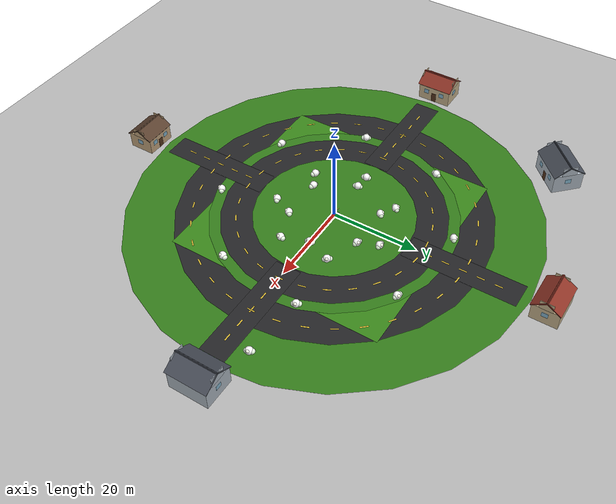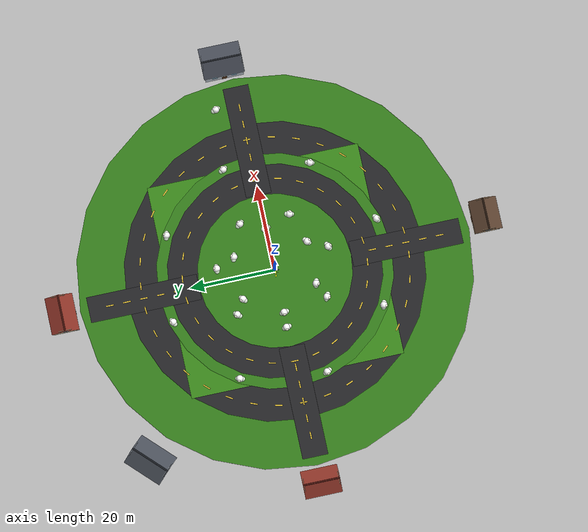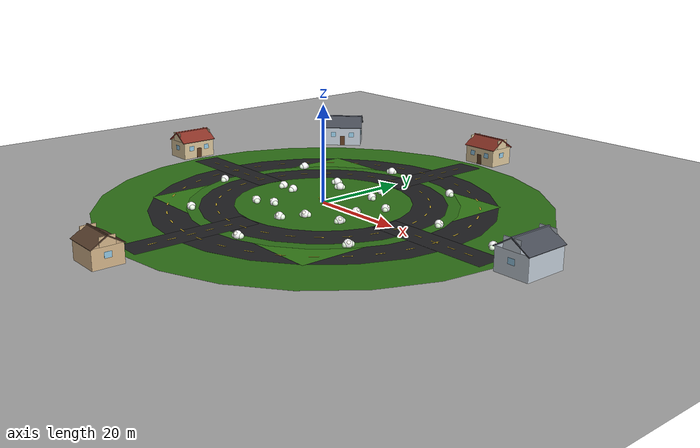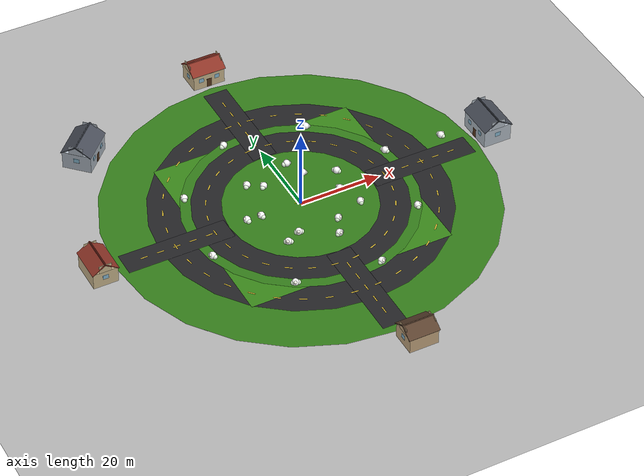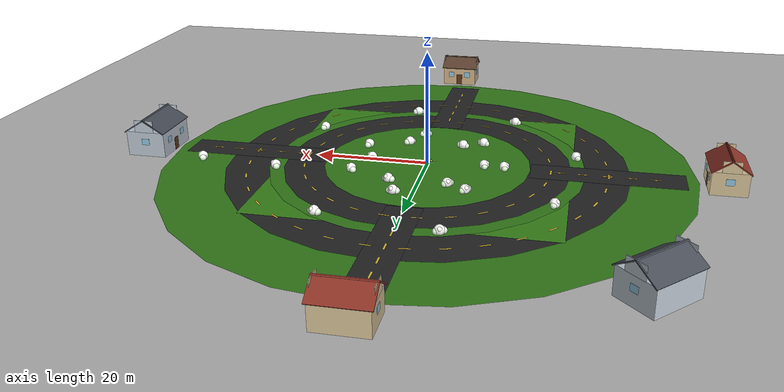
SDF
<sdf version="1.9">
 <world name="vtol_world">
  <physics name="1ms" type="ignore">
   <max_step_size>0.001</max_step_size>
   <real_time_factor>1.0</real_time_factor>
  </physics>
  <plugin filename="gz-sim-physics-system" name="gz::sim::systems::Physics"/>
  <plugin filename="gz-sim-user-commands-system" name="gz::sim::systems::UserCommands"/>
  <plugin filename="gz-sim-scene-broadcaster-system" name="gz::sim::systems::SceneBroadcaster"/>
  <scene><ambient>0.6 0.6 0.6 1</ambient><background>0.75 0.82 0.9 1</background><shadows>true</shadows></scene>
  <light name="sun" type="directional">
   <pose>0 0 10 0 0 0</pose>
   <diffuse>0.9 0.9 0.9 1</diffuse>
   <specular>0.2 0.2 0.2 1</specular>
   <direction>-0.5 0.1 -0.9</direction>
  </light>
  <light name="fill" type="directional">
   <cast_shadows>false</cast_shadows>
   <pose>0 0 10 0 0 0</pose>
   <diffuse>0.45 0.45 0.45 1</diffuse>
   <specular>0.05 0.05 0.05 1</specular>
   <direction>0.6 -0.2 -0.6</direction>
  </light>
  <model name="ground_plane">
   <static>true</static>
   <link name="link">
    <collision name="collision">
     <geometry><plane><normal>0 0 1</normal><size>200 200</size></plane></geometry>
    </collision>
    <visual name="visual">
     <geometry><plane><normal>0 0 1</normal><size>200 200</size></plane></geometry>
     <material>
      <ambient>0.7 0.7 0.7 1</ambient>
      <diffuse>0.7 0.7 0.7 1</diffuse>
      <specular>0.4 0.4 0.4 1</specular>
     </material>
    </visual>
   </link>
  </model>
  <model name="grass">
   <static>true</static>
   <link name="link">
    <visual name="visual">
     <pose>0 0 0.002 0 0 0</pose>
     <geometry><plane><normal>0 0 1</normal><size>50 50</size></plane></geometry>
     <material>
      <ambient>0.18 0.42 0.08 1</ambient>
      <diffuse>0.22 0.52 0.10 1</diffuse>
      <specular>0.05 0.12 0.03 1</specular>
     </material>
    </visual>
   </link>
  </model>
  <include><uri>model://vtol</uri><name>vtol</name><pose>0 0 0.333 1.5708 0 0</pose></include>
  <model name="road_network">
   <static>true</static>
   <link name="link">
    <visual name="grass_base">
     <pose>0 0 0.01 0 0 0</pose>
     <geometry><cylinder><radius>46.0</radius><length>0.002</length></cylinder></geometry>
     <material>
      <ambient>0.2 0.48 0.1 1</ambient>
      <diffuse>0.2 0.48 0.1 1</diffuse>
      <specular>0.05 0.05 0.05 1</specular>
     </material>
    </visual>
    <visual name="outer_asphalt">
     <pose>0 0 0.02 0 0 0</pose>
     <geometry><cylinder><radius>35.0</radius><length>0.002</length></cylinder></geometry>
     <material>
      <ambient>0.14 0.14 0.15 1</ambient>
      <diffuse>0.14 0.14 0.15 1</diffuse>
      <specular>0.05 0.05 0.05 1</specular>
     </material>
    </visual>
    <visual name="median_grass">
     <pose>0 0 0.03 0 0 0</pose>
     <geometry><cylinder><radius>27.5</radius><length>0.002</length></cylinder></geometry>
     <material>
      <ambient>0.2 0.48 0.1 1</ambient>
      <diffuse>0.2 0.48 0.1 1</diffuse>
      <specular>0.05 0.05 0.05 1</specular>
     </material>
    </visual>
    <visual name="inner_asphalt">
     <pose>0 0 0.04 0 0 0</pose>
     <geometry><cylinder><radius>25.0</radius><length>0.002</length></cylinder></geometry>
     <material>
      <ambient>0.14 0.14 0.15 1</ambient>
      <diffuse>0.14 0.14 0.15 1</diffuse>
      <specular>0.05 0.05 0.05 1</specular>
     </material>
    </visual>
    <visual name="center_grass">
     <pose>0 0 0.05 0 0 0</pose>
     <geometry><cylinder><radius>18.0</radius><length>0.002</length></cylinder></geometry>
     <material>
      <ambient>0.2 0.48 0.1 1</ambient>
      <diffuse>0.2 0.48 0.1 1</diffuse>
      <specular>0.05 0.05 0.05 1</specular>
     </material>
    </visual>
    <visual name="radial_e">
     <pose>31.000 0.000 0.055 0 0 0.0000</pose>
     <geometry><plane><normal>0 0 1</normal><size>26.0 6.0</size></plane></geometry>
     <material>
      <ambient>0.14 0.14 0.15 1</ambient>
      <diffuse>0.14 0.14 0.15 1</diffuse>
      <specular>0.05 0.05 0.05 1</specular>
     </material>
    </visual>
    <visual name="radial_n">
     <pose>0.000 31.000 0.055 0 0 0.0000</pose>
     <geometry><plane><normal>0 0 1</normal><size>6.0 26.0</size></plane></geometry>
     <material>
      <ambient>0.14 0.14 0.15 1</ambient>
      <diffuse>0.14 0.14 0.15 1</diffuse>
      <specular>0.05 0.05 0.05 1</specular>
     </material>
    </visual>
    <visual name="radial_w">
     <pose>-31.000 0.000 0.055 0 0 0.0000</pose>
     <geometry><plane><normal>0 0 1</normal><size>26.0 6.0</size></plane></geometry>
     <material>
      <ambient>0.14 0.14 0.15 1</ambient>
      <diffuse>0.14 0.14 0.15 1</diffuse>
      <specular>0.05 0.05 0.05 1</specular>
     </material>
    </visual>
    <visual name="radial_s">
     <pose>-0.000 -31.000 0.055 0 0 0.0000</pose>
     <geometry><plane><normal>0 0 1</normal><size>6.0 26.0</size></plane></geometry>
     <material>
      <ambient>0.14 0.14 0.15 1</ambient>
      <diffuse>0.14 0.14 0.15 1</diffuse>
      <specular>0.05 0.05 0.05 1</specular>
     </material>
    </visual>
    <visual name="din_0">
     <pose>21.500 0.000 0.06 0 0 1.5708</pose>
     <geometry><plane><normal>0 0 1</normal><size>1.8 0.3</size></plane></geometry>
     <material>
      <ambient>0.85 0.72 0.2 1</ambient>
      <diffuse>0.85 0.72 0.2 1</diffuse>
      <specular>0.05 0.05 0.05 1</specular>
     </material>
    </visual>
    <visual name="din_1">
     <pose>20.875 5.145 0.06 0 0 1.8125</pose>
     <geometry><plane><normal>0 0 1</normal><size>1.8 0.3</size></plane></geometry>
     <material>
      <ambient>0.85 0.72 0.2 1</ambient>
      <diffuse>0.85 0.72 0.2 1</diffuse>
      <specular>0.05 0.05 0.05 1</specular>
     </material>
    </visual>
    <visual name="din_2">
     <pose>19.037 9.992 0.06 0 0 2.0541</pose>
     <geometry><plane><normal>0 0 1</normal><size>1.8 0.3</size></plane></geometry>
     <material>
      <ambient>0.85 0.72 0.2 1</ambient>
      <diffuse>0.85 0.72 0.2 1</diffuse>
      <specular>0.05 0.05 0.05 1</specular>
     </material>
    </visual>
    <visual name="din_3">
     <pose>16.093 14.257 0.06 0 0 2.2958</pose>
     <geometry><plane><normal>0 0 1</normal><size>1.8 0.3</size></plane></geometry>
     <material>
      <ambient>0.85 0.72 0.2 1</ambient>
      <diffuse>0.85 0.72 0.2 1</diffuse>
      <specular>0.05 0.05 0.05 1</specular>
     </material>
    </visual>
    <visual name="din_4">
     <pose>12.213 17.694 0.06 0 0 2.5374</pose>
     <geometry><plane><normal>0 0 1</normal><size>1.8 0.3</size></plane></geometry>
     <material>
      <ambient>0.85 0.72 0.2 1</ambient>
      <diffuse>0.85 0.72 0.2 1</diffuse>
      <specular>0.05 0.05 0.05 1</specular>
     </material>
    </visual>
    <visual name="din_5">
     <pose>7.624 20.103 0.06 0 0 2.7791</pose>
     <geometry><plane><normal>0 0 1</normal><size>1.8 0.3</size></plane></geometry>
     <material>
      <ambient>0.85 0.72 0.2 1</ambient>
      <diffuse>0.85 0.72 0.2 1</diffuse>
      <specular>0.05 0.05 0.05 1</specular>
     </material>
    </visual>
    <visual name="din_6">
     <pose>2.592 21.343 0.06 0 0 3.0208</pose>
     <geometry><plane><normal>0 0 1</normal><size>1.8 0.3</size></plane></geometry>
     <material>
      <ambient>0.85 0.72 0.2 1</ambient>
      <diffuse>0.85 0.72 0.2 1</diffuse>
      <specular>0.05 0.05 0.05 1</specular>
     </material>
    </visual>
    <visual name="din_7">
     <pose>-2.592 21.343 0.06 0 0 3.2624</pose>
     <geometry><plane><normal>0 0 1</normal><size>1.8 0.3</size></plane></geometry>
     <material>
      <ambient>0.85 0.72 0.2 1</ambient>
      <diffuse>0.85 0.72 0.2 1</diffuse>
      <specular>0.05 0.05 0.05 1</specular>
     </material>
    </visual>
    <visual name="din_8">
     <pose>-7.624 20.103 0.06 0 0 3.5041</pose>
     <geometry><plane><normal>0 0 1</normal><size>1.8 0.3</size></plane></geometry>
     <material>
      <ambient>0.85 0.72 0.2 1</ambient>
      <diffuse>0.85 0.72 0.2 1</diffuse>
      <specular>0.05 0.05 0.05 1</specular>
     </material>
    </visual>
    <visual name="din_9">
     <pose>-12.213 17.694 0.06 0 0 3.7457</pose>
     <geometry><plane><normal>0 0 1</normal><size>1.8 0.3</size></plane></geometry>
     <material>
      <ambient>0.85 0.72 0.2 1</ambient>
      <diffuse>0.85 0.72 0.2 1</diffuse>
      <specular>0.05 0.05 0.05 1</specular>
     </material>
    </visual>
    <visual name="din_10">
     <pose>-16.093 14.257 0.06 0 0 3.9874</pose>
     <geometry><plane><normal>0 0 1</normal><size>1.8 0.3</size></plane></geometry>
     <material>
      <ambient>0.85 0.72 0.2 1</ambient>
      <diffuse>0.85 0.72 0.2 1</diffuse>
      <specular>0.05 0.05 0.05 1</specular>
     </material>
    </visual>
    <visual name="din_11">
     <pose>-19.037 9.992 0.06 0 0 4.2291</pose>
     <geometry><plane><normal>0 0 1</normal><size>1.8 0.3</size></plane></geometry>
     <material>
      <ambient>0.85 0.72 0.2 1</ambient>
      <diffuse>0.85 0.72 0.2 1</diffuse>
      <specular>0.05 0.05 0.05 1</specular>
     </material>
    </visual>
    <visual name="din_12">
     <pose>-20.875 5.145 0.06 0 0 4.4707</pose>
     <geometry><plane><normal>0 0 1</normal><size>1.8 0.3</size></plane></geometry>
     <material>
      <ambient>0.85 0.72 0.2 1</ambient>
      <diffuse>0.85 0.72 0.2 1</diffuse>
      <specular>0.05 0.05 0.05 1</specular>
     </material>
    </visual>
    <visual name="din_13">
     <pose>-21.500 -0.000 0.06 0 0 4.7124</pose>
     <geometry><plane><normal>0 0 1</normal><size>1.8 0.3</size></plane></geometry>
     <material>
      <ambient>0.85 0.72 0.2 1</ambient>
      <diffuse>0.85 0.72 0.2 1</diffuse>
      <specular>0.05 0.05 0.05 1</specular>
     </material>
    </visual>
    <visual name="din_14">
     <pose>-20.875 -5.145 0.06 0 0 4.9540</pose>
     <geometry><plane><normal>0 0 1</normal><size>1.8 0.3</size></plane></geometry>
     <material>
      <ambient>0.85 0.72 0.2 1</ambient>
      <diffuse>0.85 0.72 0.2 1</diffuse>
      <specular>0.05 0.05 0.05 1</specular>
     </material>
    </visual>
    <visual name="din_15">
     <pose>-19.037 -9.992 0.06 0 0 5.1957</pose>
     <geometry><plane><normal>0 0 1</normal><size>1.8 0.3</size></plane></geometry>
     <material>
      <ambient>0.85 0.72 0.2 1</ambient>
      <diffuse>0.85 0.72 0.2 1</diffuse>
      <specular>0.05 0.05 0.05 1</specular>
     </material>
    </visual>
    <visual name="din_16">
     <pose>-16.093 -14.257 0.06 0 0 5.4374</pose>
     <geometry><plane><normal>0 0 1</normal><size>1.8 0.3</size></plane></geometry>
     <material>
      <ambient>0.85 0.72 0.2 1</ambient>
      <diffuse>0.85 0.72 0.2 1</diffuse>
      <specular>0.05 0.05 0.05 1</specular>
     </material>
    </visual>
    <visual name="din_17">
     <pose>-12.213 -17.694 0.06 0 0 5.6790</pose>
     <geometry><plane><normal>0 0 1</normal><size>1.8 0.3</size></plane></geometry>
     <material>
      <ambient>0.85 0.72 0.2 1</ambient>
      <diffuse>0.85 0.72 0.2 1</diffuse>
      <specular>0.05 0.05 0.05 1</specular>
     </material>
    </visual>
    <visual name="din_18">
     <pose>-7.624 -20.103 0.06 0 0 5.9207</pose>
     <geometry><plane><normal>0 0 1</normal><size>1.8 0.3</size></plane></geometry>
     <material>
      <ambient>0.85 0.72 0.2 1</ambient>
      <diffuse>0.85 0.72 0.2 1</diffuse>
      <specular>0.05 0.05 0.05 1</specular>
     </material>
    </visual>
    <visual name="din_19">
     <pose>-2.592 -21.343 0.06 0 0 6.1624</pose>
     <geometry><plane><normal>0 0 1</normal><size>1.8 0.3</size></plane></geometry>
     <material>
      <ambient>0.85 0.72 0.2 1</ambient>
      <diffuse>0.85 0.72 0.2 1</diffuse>
      <specular>0.05 0.05 0.05 1</specular>
     </material>
    </visual>
    <visual name="din_20">
     <pose>2.592 -21.343 0.06 0 0 6.4040</pose>
     <geometry><plane><normal>0 0 1</normal><size>1.8 0.3</size></plane></geometry>
     <material>
      <ambient>0.85 0.72 0.2 1</ambient>
      <diffuse>0.85 0.72 0.2 1</diffuse>
      <specular>0.05 0.05 0.05 1</specular>
     </material>
    </visual>
    <visual name="din_21">
     <pose>7.624 -20.103 0.06 0 0 6.6457</pose>
     <geometry><plane><normal>0 0 1</normal><size>1.8 0.3</size></plane></geometry>
     <material>
      <ambient>0.85 0.72 0.2 1</ambient>
      <diffuse>0.85 0.72 0.2 1</diffuse>
      <specular>0.05 0.05 0.05 1</specular>
     </material>
    </visual>
    <visual name="din_22">
     <pose>12.213 -17.694 0.06 0 0 6.8873</pose>
     <geometry><plane><normal>0 0 1</normal><size>1.8 0.3</size></plane></geometry>
     <material>
      <ambient>0.85 0.72 0.2 1</ambient>
      <diffuse>0.85 0.72 0.2 1</diffuse>
      <specular>0.05 0.05 0.05 1</specular>
     </material>
    </visual>
    <visual name="din_23">
     <pose>16.093 -14.257 0.06 0 0 7.1290</pose>
     <geometry><plane><normal>0 0 1</normal><size>1.8 0.3</size></plane></geometry>
     <material>
      <ambient>0.85 0.72 0.2 1</ambient>
      <diffuse>0.85 0.72 0.2 1</diffuse>
      <specular>0.05 0.05 0.05 1</specular>
     </material>
    </visual>
    <visual name="din_24">
     <pose>19.037 -9.992 0.06 0 0 7.3707</pose>
     <geometry><plane><normal>0 0 1</normal><size>1.8 0.3</size></plane></geometry>
     <material>
      <ambient>0.85 0.72 0.2 1</ambient>
      <diffuse>0.85 0.72 0.2 1</diffuse>
      <specular>0.05 0.05 0.05 1</specular>
     </material>
    </visual>
    <visual name="din_25">
     <pose>20.875 -5.145 0.06 0 0 7.6123</pose>
     <geometry><plane><normal>0 0 1</normal><size>1.8 0.3</size></plane></geometry>
     <material>
      <ambient>0.85 0.72 0.2 1</ambient>
      <diffuse>0.85 0.72 0.2 1</diffuse>
      <specular>0.05 0.05 0.05 1</specular>
     </material>
    </visual>
    <visual name="dout_0">
     <pose>31.250 0.000 0.06 0 0 1.5708</pose>
     <geometry><plane><normal>0 0 1</normal><size>1.8 0.3</size></plane></geometry>
     <material>
      <ambient>0.85 0.72 0.2 1</ambient>
      <diffuse>0.85 0.72 0.2 1</diffuse>
      <specular>0.05 0.05 0.05 1</specular>
     </material>
    </visual>
    <visual name="dout_1">
     <pose>30.718 5.742 0.06 0 0 1.7556</pose>
     <geometry><plane><normal>0 0 1</normal><size>1.8 0.3</size></plane></geometry>
     <material>
      <ambient>0.85 0.72 0.2 1</ambient>
      <diffuse>0.85 0.72 0.2 1</diffuse>
      <specular>0.05 0.05 0.05 1</specular>
     </material>
    </visual>
    <visual name="dout_2">
     <pose>29.140 11.289 0.06 0 0 1.9404</pose>
     <geometry><plane><normal>0 0 1</normal><size>1.8 0.3</size></plane></geometry>
     <material>
      <ambient>0.85 0.72 0.2 1</ambient>
      <diffuse>0.85 0.72 0.2 1</diffuse>
      <specular>0.05 0.05 0.05 1</specular>
     </material>
    </visual>
    <visual name="dout_3">
     <pose>26.569 16.451 0.06 0 0 2.1252</pose>
     <geometry><plane><normal>0 0 1</normal><size>1.8 0.3</size></plane></geometry>
     <material>
      <ambient>0.85 0.72 0.2 1</ambient>
      <diffuse>0.85 0.72 0.2 1</diffuse>
      <specular>0.05 0.05 0.05 1</specular>
     </material>
    </visual>
    <visual name="dout_4">
     <pose>23.094 21.053 0.06 0 0 2.3100</pose>
     <geometry><plane><normal>0 0 1</normal><size>1.8 0.3</size></plane></geometry>
     <material>
      <ambient>0.85 0.72 0.2 1</ambient>
      <diffuse>0.85 0.72 0.2 1</diffuse>
      <specular>0.05 0.05 0.05 1</specular>
     </material>
    </visual>
    <visual name="dout_5">
     <pose>18.832 24.938 0.06 0 0 2.4948</pose>
     <geometry><plane><normal>0 0 1</normal><size>1.8 0.3</size></plane></geometry>
     <material>
      <ambient>0.85 0.72 0.2 1</ambient>
      <diffuse>0.85 0.72 0.2 1</diffuse>
      <specular>0.05 0.05 0.05 1</specular>
     </material>
    </visual>
    <visual name="dout_6">
     <pose>13.929 27.974 0.06 0 0 2.6796</pose>
     <geometry><plane><normal>0 0 1</normal><size>1.8 0.3</size></plane></geometry>
     <material>
      <ambient>0.85 0.72 0.2 1</ambient>
      <diffuse>0.85 0.72 0.2 1</diffuse>
      <specular>0.05 0.05 0.05 1</specular>
     </material>
    </visual>
    <visual name="dout_7">
     <pose>8.552 30.057 0.06 0 0 2.8644</pose>
     <geometry><plane><normal>0 0 1</normal><size>1.8 0.3</size></plane></geometry>
     <material>
      <ambient>0.85 0.72 0.2 1</ambient>
      <diffuse>0.85 0.72 0.2 1</diffuse>
      <specular>0.05 0.05 0.05 1</specular>
     </material>
    </visual>
    <visual name="dout_8">
     <pose>2.883 31.117 0.06 0 0 3.0492</pose>
     <geometry><plane><normal>0 0 1</normal><size>1.8 0.3</size></plane></geometry>
     <material>
      <ambient>0.85 0.72 0.2 1</ambient>
      <diffuse>0.85 0.72 0.2 1</diffuse>
      <specular>0.05 0.05 0.05 1</specular>
     </material>
    </visual>
    <visual name="dout_9">
     <pose>-2.883 31.117 0.06 0 0 3.2340</pose>
     <geometry><plane><normal>0 0 1</normal><size>1.8 0.3</size></plane></geometry>
     <material>
      <ambient>0.85 0.72 0.2 1</ambient>
      <diffuse>0.85 0.72 0.2 1</diffuse>
      <specular>0.05 0.05 0.05 1</specular>
     </material>
    </visual>
    <visual name="dout_10">
     <pose>-8.552 30.057 0.06 0 0 3.4188</pose>
     <geometry><plane><normal>0 0 1</normal><size>1.8 0.3</size></plane></geometry>
     <material>
      <ambient>0.85 0.72 0.2 1</ambient>
      <diffuse>0.85 0.72 0.2 1</diffuse>
      <specular>0.05 0.05 0.05 1</specular>
     </material>
    </visual>
    <visual name="dout_11">
     <pose>-13.929 27.974 0.06 0 0 3.6036</pose>
     <geometry><plane><normal>0 0 1</normal><size>1.8 0.3</size></plane></geometry>
     <material>
      <ambient>0.85 0.72 0.2 1</ambient>
      <diffuse>0.85 0.72 0.2 1</diffuse>
      <specular>0.05 0.05 0.05 1</specular>
     </material>
    </visual>
    <visual name="dout_12">
     <pose>-18.832 24.938 0.06 0 0 3.7884</pose>
     <geometry><plane><normal>0 0 1</normal><size>1.8 0.3</size></plane></geometry>
     <material>
      <ambient>0.85 0.72 0.2 1</ambient>
      <diffuse>0.85 0.72 0.2 1</diffuse>
      <specular>0.05 0.05 0.05 1</specular>
     </material>
    </visual>
    <visual name="dout_13">
     <pose>-23.094 21.053 0.06 0 0 3.9732</pose>
     <geometry><plane><normal>0 0 1</normal><size>1.8 0.3</size></plane></geometry>
     <material>
      <ambient>0.85 0.72 0.2 1</ambient>
      <diffuse>0.85 0.72 0.2 1</diffuse>
      <specular>0.05 0.05 0.05 1</specular>
     </material>
    </visual>
    <visual name="dout_14">
     <pose>-26.569 16.451 0.06 0 0 4.1580</pose>
     <geometry><plane><normal>0 0 1</normal><size>1.8 0.3</size></plane></geometry>
     <material>
      <ambient>0.85 0.72 0.2 1</ambient>
      <diffuse>0.85 0.72 0.2 1</diffuse>
      <specular>0.05 0.05 0.05 1</specular>
     </material>
    </visual>
    <visual name="dout_15">
     <pose>-29.140 11.289 0.06 0 0 4.3428</pose>
     <geometry><plane><normal>0 0 1</normal><size>1.8 0.3</size></plane></geometry>
     <material>
      <ambient>0.85 0.72 0.2 1</ambient>
      <diffuse>0.85 0.72 0.2 1</diffuse>
      <specular>0.05 0.05 0.05 1</specular>
     </material>
    </visual>
    <visual name="dout_16">
     <pose>-30.718 5.742 0.06 0 0 4.5276</pose>
     <geometry><plane><normal>0 0 1</normal><size>1.8 0.3</size></plane></geometry>
     <material>
      <ambient>0.85 0.72 0.2 1</ambient>
      <diffuse>0.85 0.72 0.2 1</diffuse>
      <specular>0.05 0.05 0.05 1</specular>
     </material>
    </visual>
    <visual name="dout_17">
     <pose>-31.250 0.000 0.06 0 0 4.7124</pose>
     <geometry><plane><normal>0 0 1</normal><size>1.8 0.3</size></plane></geometry>
     <material>
      <ambient>0.85 0.72 0.2 1</ambient>
      <diffuse>0.85 0.72 0.2 1</diffuse>
      <specular>0.05 0.05 0.05 1</specular>
     </material>
    </visual>
    <visual name="dout_18">
     <pose>-30.718 -5.742 0.06 0 0 4.8972</pose>
     <geometry><plane><normal>0 0 1</normal><size>1.8 0.3</size></plane></geometry>
     <material>
      <ambient>0.85 0.72 0.2 1</ambient>
      <diffuse>0.85 0.72 0.2 1</diffuse>
      <specular>0.05 0.05 0.05 1</specular>
     </material>
    </visual>
    <visual name="dout_19">
     <pose>-29.140 -11.289 0.06 0 0 5.0820</pose>
     <geometry><plane><normal>0 0 1</normal><size>1.8 0.3</size></plane></geometry>
     <material>
      <ambient>0.85 0.72 0.2 1</ambient>
      <diffuse>0.85 0.72 0.2 1</diffuse>
      <specular>0.05 0.05 0.05 1</specular>
     </material>
    </visual>
    <visual name="dout_20">
     <pose>-26.569 -16.451 0.06 0 0 5.2668</pose>
     <geometry><plane><normal>0 0 1</normal><size>1.8 0.3</size></plane></geometry>
     <material>
      <ambient>0.85 0.72 0.2 1</ambient>
      <diffuse>0.85 0.72 0.2 1</diffuse>
      <specular>0.05 0.05 0.05 1</specular>
     </material>
    </visual>
    <visual name="dout_21">
     <pose>-23.094 -21.053 0.06 0 0 5.4516</pose>
     <geometry><plane><normal>0 0 1</normal><size>1.8 0.3</size></plane></geometry>
     <material>
      <ambient>0.85 0.72 0.2 1</ambient>
      <diffuse>0.85 0.72 0.2 1</diffuse>
      <specular>0.05 0.05 0.05 1</specular>
     </material>
    </visual>
    <visual name="dout_22">
     <pose>-18.832 -24.938 0.06 0 0 5.6364</pose>
     <geometry><plane><normal>0 0 1</normal><size>1.8 0.3</size></plane></geometry>
     <material>
      <ambient>0.85 0.72 0.2 1</ambient>
      <diffuse>0.85 0.72 0.2 1</diffuse>
      <specular>0.05 0.05 0.05 1</specular>
     </material>
    </visual>
    <visual name="dout_23">
     <pose>-13.929 -27.974 0.06 0 0 5.8212</pose>
     <geometry><plane><normal>0 0 1</normal><size>1.8 0.3</size></plane></geometry>
     <material>
      <ambient>0.85 0.72 0.2 1</ambient>
      <diffuse>0.85 0.72 0.2 1</diffuse>
      <specular>0.05 0.05 0.05 1</specular>
     </material>
    </visual>
    <visual name="dout_24">
     <pose>-8.552 -30.057 0.06 0 0 6.0060</pose>
     <geometry><plane><normal>0 0 1</normal><size>1.8 0.3</size></plane></geometry>
     <material>
      <ambient>0.85 0.72 0.2 1</ambient>
      <diffuse>0.85 0.72 0.2 1</diffuse>
      <specular>0.05 0.05 0.05 1</specular>
     </material>
    </visual>
    <visual name="dout_25">
     <pose>-2.883 -31.117 0.06 0 0 6.1908</pose>
     <geometry><plane><normal>0 0 1</normal><size>1.8 0.3</size></plane></geometry>
     <material>
      <ambient>0.85 0.72 0.2 1</ambient>
      <diffuse>0.85 0.72 0.2 1</diffuse>
      <specular>0.05 0.05 0.05 1</specular>
     </material>
    </visual>
    <visual name="dout_26">
     <pose>2.883 -31.117 0.06 0 0 6.3756</pose>
     <geometry><plane><normal>0 0 1</normal><size>1.8 0.3</size></plane></geometry>
     <material>
      <ambient>0.85 0.72 0.2 1</ambient>
      <diffuse>0.85 0.72 0.2 1</diffuse>
      <specular>0.05 0.05 0.05 1</specular>
     </material>
    </visual>
    <visual name="dout_27">
     <pose>8.552 -30.057 0.06 0 0 6.5604</pose>
     <geometry><plane><normal>0 0 1</normal><size>1.8 0.3</size></plane></geometry>
     <material>
      <ambient>0.85 0.72 0.2 1</ambient>
      <diffuse>0.85 0.72 0.2 1</diffuse>
      <specular>0.05 0.05 0.05 1</specular>
     </material>
    </visual>
    <visual name="dout_28">
     <pose>13.929 -27.974 0.06 0 0 6.7452</pose>
     <geometry><plane><normal>0 0 1</normal><size>1.8 0.3</size></plane></geometry>
     <material>
      <ambient>0.85 0.72 0.2 1</ambient>
      <diffuse>0.85 0.72 0.2 1</diffuse>
      <specular>0.05 0.05 0.05 1</specular>
     </material>
    </visual>
    <visual name="dout_29">
     <pose>18.832 -24.938 0.06 0 0 6.9300</pose>
     <geometry><plane><normal>0 0 1</normal><size>1.8 0.3</size></plane></geometry>
     <material>
      <ambient>0.85 0.72 0.2 1</ambient>
      <diffuse>0.85 0.72 0.2 1</diffuse>
      <specular>0.05 0.05 0.05 1</specular>
     </material>
    </visual>
    <visual name="dout_30">
     <pose>23.094 -21.053 0.06 0 0 7.1148</pose>
     <geometry><plane><normal>0 0 1</normal><size>1.8 0.3</size></plane></geometry>
     <material>
      <ambient>0.85 0.72 0.2 1</ambient>
      <diffuse>0.85 0.72 0.2 1</diffuse>
      <specular>0.05 0.05 0.05 1</specular>
     </material>
    </visual>
    <visual name="dout_31">
     <pose>26.569 -16.451 0.06 0 0 7.2996</pose>
     <geometry><plane><normal>0 0 1</normal><size>1.8 0.3</size></plane></geometry>
     <material>
      <ambient>0.85 0.72 0.2 1</ambient>
      <diffuse>0.85 0.72 0.2 1</diffuse>
      <specular>0.05 0.05 0.05 1</specular>
     </material>
    </visual>
    <visual name="dout_32">
     <pose>29.140 -11.289 0.06 0 0 7.4844</pose>
     <geometry><plane><normal>0 0 1</normal><size>1.8 0.3</size></plane></geometry>
     <material>
      <ambient>0.85 0.72 0.2 1</ambient>
      <diffuse>0.85 0.72 0.2 1</diffuse>
      <specular>0.05 0.05 0.05 1</specular>
     </material>
    </visual>
    <visual name="dout_33">
     <pose>30.718 -5.742 0.06 0 0 7.6692</pose>
     <geometry><plane><normal>0 0 1</normal><size>1.8 0.3</size></plane></geometry>
     <material>
      <ambient>0.85 0.72 0.2 1</ambient>
      <diffuse>0.85 0.72 0.2 1</diffuse>
      <specular>0.05 0.05 0.05 1</specular>
     </material>
    </visual>
    <visual name="drad_1">
     <pose>23.000 0.000 0.06 0 0 0.0000</pose>
     <geometry><plane><normal>0 0 1</normal><size>1.8 0.3</size></plane></geometry>
     <material>
      <ambient>0.85 0.72 0.2 1</ambient>
      <diffuse>0.85 0.72 0.2 1</diffuse>
      <specular>0.05 0.05 0.05 1</specular>
     </material>
    </visual>
    <visual name="drad_2">
     <pose>27.000 0.000 0.06 0 0 0.0000</pose>
     <geometry><plane><normal>0 0 1</normal><size>1.8 0.3</size></plane></geometry>
     <material>
      <ambient>0.85 0.72 0.2 1</ambient>
      <diffuse>0.85 0.72 0.2 1</diffuse>
      <specular>0.05 0.05 0.05 1</specular>
     </material>
    </visual>
    <visual name="drad_3">
     <pose>31.000 0.000 0.06 0 0 0.0000</pose>
     <geometry><plane><normal>0 0 1</normal><size>1.8 0.3</size></plane></geometry>
     <material>
      <ambient>0.85 0.72 0.2 1</ambient>
      <diffuse>0.85 0.72 0.2 1</diffuse>
      <specular>0.05 0.05 0.05 1</specular>
     </material>
    </visual>
    <visual name="drad_4">
     <pose>35.000 0.000 0.06 0 0 0.0000</pose>
     <geometry><plane><normal>0 0 1</normal><size>1.8 0.3</size></plane></geometry>
     <material>
      <ambient>0.85 0.72 0.2 1</ambient>
      <diffuse>0.85 0.72 0.2 1</diffuse>
      <specular>0.05 0.05 0.05 1</specular>
     </material>
    </visual>
    <visual name="drad_5">
     <pose>39.000 0.000 0.06 0 0 0.0000</pose>
     <geometry><plane><normal>0 0 1</normal><size>1.8 0.3</size></plane></geometry>
     <material>
      <ambient>0.85 0.72 0.2 1</ambient>
      <diffuse>0.85 0.72 0.2 1</diffuse>
      <specular>0.05 0.05 0.05 1</specular>
     </material>
    </visual>
    <visual name="drad_6">
     <pose>0.000 23.000 0.06 0 0 0.0000</pose>
     <geometry><plane><normal>0 0 1</normal><size>0.3 1.8</size></plane></geometry>
     <material>
      <ambient>0.85 0.72 0.2 1</ambient>
      <diffuse>0.85 0.72 0.2 1</diffuse>
      <specular>0.05 0.05 0.05 1</specular>
     </material>
    </visual>
    <visual name="drad_7">
     <pose>0.000 27.000 0.06 0 0 0.0000</pose>
     <geometry><plane><normal>0 0 1</normal><size>0.3 1.8</size></plane></geometry>
     <material>
      <ambient>0.85 0.72 0.2 1</ambient>
      <diffuse>0.85 0.72 0.2 1</diffuse>
      <specular>0.05 0.05 0.05 1</specular>
     </material>
    </visual>
    <visual name="drad_8">
     <pose>0.000 31.000 0.06 0 0 0.0000</pose>
     <geometry><plane><normal>0 0 1</normal><size>0.3 1.8</size></plane></geometry>
     <material>
      <ambient>0.85 0.72 0.2 1</ambient>
      <diffuse>0.85 0.72 0.2 1</diffuse>
      <specular>0.05 0.05 0.05 1</specular>
     </material>
    </visual>
    <visual name="drad_9">
     <pose>0.000 35.000 0.06 0 0 0.0000</pose>
     <geometry><plane><normal>0 0 1</normal><size>0.3 1.8</size></plane></geometry>
     <material>
      <ambient>0.85 0.72 0.2 1</ambient>
      <diffuse>0.85 0.72 0.2 1</diffuse>
      <specular>0.05 0.05 0.05 1</specular>
     </material>
    </visual>
    <visual name="drad_10">
     <pose>0.000 39.000 0.06 0 0 0.0000</pose>
     <geometry><plane><normal>0 0 1</normal><size>0.3 1.8</size></plane></geometry>
     <material>
      <ambient>0.85 0.72 0.2 1</ambient>
      <diffuse>0.85 0.72 0.2 1</diffuse>
      <specular>0.05 0.05 0.05 1</specular>
     </material>
    </visual>
    <visual name="drad_11">
     <pose>-23.000 0.000 0.06 0 0 0.0000</pose>
     <geometry><plane><normal>0 0 1</normal><size>1.8 0.3</size></plane></geometry>
     <material>
      <ambient>0.85 0.72 0.2 1</ambient>
      <diffuse>0.85 0.72 0.2 1</diffuse>
      <specular>0.05 0.05 0.05 1</specular>
     </material>
    </visual>
    <visual name="drad_12">
     <pose>-27.000 0.000 0.06 0 0 0.0000</pose>
     <geometry><plane><normal>0 0 1</normal><size>1.8 0.3</size></plane></geometry>
     <material>
      <ambient>0.85 0.72 0.2 1</ambient>
      <diffuse>0.85 0.72 0.2 1</diffuse>
      <specular>0.05 0.05 0.05 1</specular>
     </material>
    </visual>
    <visual name="drad_13">
     <pose>-31.000 0.000 0.06 0 0 0.0000</pose>
     <geometry><plane><normal>0 0 1</normal><size>1.8 0.3</size></plane></geometry>
     <material>
      <ambient>0.85 0.72 0.2 1</ambient>
      <diffuse>0.85 0.72 0.2 1</diffuse>
      <specular>0.05 0.05 0.05 1</specular>
     </material>
    </visual>
    <visual name="drad_14">
     <pose>-35.000 0.000 0.06 0 0 0.0000</pose>
     <geometry><plane><normal>0 0 1</normal><size>1.8 0.3</size></plane></geometry>
     <material>
      <ambient>0.85 0.72 0.2 1</ambient>
      <diffuse>0.85 0.72 0.2 1</diffuse>
      <specular>0.05 0.05 0.05 1</specular>
     </material>
    </visual>
    <visual name="drad_15">
     <pose>-39.000 0.000 0.06 0 0 0.0000</pose>
     <geometry><plane><normal>0 0 1</normal><size>1.8 0.3</size></plane></geometry>
     <material>
      <ambient>0.85 0.72 0.2 1</ambient>
      <diffuse>0.85 0.72 0.2 1</diffuse>
      <specular>0.05 0.05 0.05 1</specular>
     </material>
    </visual>
    <visual name="drad_16">
     <pose>-0.000 -23.000 0.06 0 0 0.0000</pose>
     <geometry><plane><normal>0 0 1</normal><size>0.3 1.8</size></plane></geometry>
     <material>
      <ambient>0.85 0.72 0.2 1</ambient>
      <diffuse>0.85 0.72 0.2 1</diffuse>
      <specular>0.05 0.05 0.05 1</specular>
     </material>
    </visual>
    <visual name="drad_17">
     <pose>-0.000 -27.000 0.06 0 0 0.0000</pose>
     <geometry><plane><normal>0 0 1</normal><size>0.3 1.8</size></plane></geometry>
     <material>
      <ambient>0.85 0.72 0.2 1</ambient>
      <diffuse>0.85 0.72 0.2 1</diffuse>
      <specular>0.05 0.05 0.05 1</specular>
     </material>
    </visual>
    <visual name="drad_18">
     <pose>-0.000 -31.000 0.06 0 0 0.0000</pose>
     <geometry><plane><normal>0 0 1</normal><size>0.3 1.8</size></plane></geometry>
     <material>
      <ambient>0.85 0.72 0.2 1</ambient>
      <diffuse>0.85 0.72 0.2 1</diffuse>
      <specular>0.05 0.05 0.05 1</specular>
     </material>
    </visual>
    <visual name="drad_19">
     <pose>-0.000 -35.000 0.06 0 0 0.0000</pose>
     <geometry><plane><normal>0 0 1</normal><size>0.3 1.8</size></plane></geometry>
     <material>
      <ambient>0.85 0.72 0.2 1</ambient>
      <diffuse>0.85 0.72 0.2 1</diffuse>
      <specular>0.05 0.05 0.05 1</specular>
     </material>
    </visual>
    <visual name="drad_20">
     <pose>-0.000 -39.000 0.06 0 0 0.0000</pose>
     <geometry><plane><normal>0 0 1</normal><size>0.3 1.8</size></plane></geometry>
     <material>
      <ambient>0.85 0.72 0.2 1</ambient>
      <diffuse>0.85 0.72 0.2 1</diffuse>
      <specular>0.05 0.05 0.05 1</specular>
     </material>
    </visual>
   </link>
  </model>
  <include><uri>model://house1</uri><name>house_1</name><pose>0 50 0 0 0 3.1416</pose></include>
  <include><uri>model://house2</uri><name>house_2</name><pose>50 2 0 0 0 1.5708</pose></include>
  <include><uri>model://house3</uri><name>house_3</name><pose>2 -50 0 0 0 0.0</pose></include>
  <include><uri>model://house1</uri><name>house_4</name><pose>-50 0 0 0 0 -1.5708</pose></include>
  <include><uri>model://house2</uri><name>house_5</name><pose>-37 37 0 0 0 -2.356</pose></include>
  <include><uri>model://bush</uri><name>bush_1</name><pose>10.0 0.0 0 0 0 1.3</pose></include>
  <include><uri>model://bush</uri><name>bush_2</name><pose>5.0 8.66 0 0 0 2.347</pose></include>
  <include><uri>model://bush</uri><name>bush_3</name><pose>-5.0 8.66 0 0 0 3.394</pose></include>
  <include><uri>model://bush</uri><name>bush_4</name><pose>-10.0 0.0 0 0 0 4.442</pose></include>
  <include><uri>model://bush</uri><name>bush_5</name><pose>-5.0 -8.66 0 0 0 5.489</pose></include>
  <include><uri>model://bush</uri><name>bush_6</name><pose>5.0 -8.66 0 0 0 0.253</pose></include>
  <include><uri>model://bush</uri><name>bush_7</name><pose>12.24 5.71 0 0 0 1.736</pose></include>
  <include><uri>model://bush</uri><name>bush_8</name><pose>3.17 13.12 0 0 0 2.634</pose></include>
  <include><uri>model://bush</uri><name>bush_9</name><pose>-8.28 10.66 0 0 0 3.532</pose></include>
  <include><uri>model://bush</uri><name>bush_10</name><pose>-13.5 0.17 0 0 0 4.429</pose></include>
  <include><uri>model://bush</uri><name>bush_11</name><pose>-8.55 -10.45 0 0 0 5.327</pose></include>
  <include><uri>model://bush</uri><name>bush_12</name><pose>2.84 -13.2 0 0 0 6.224</pose></include>
  <include><uri>model://bush</uri><name>bush_13</name><pose>12.09 -6.01 0 0 0 0.839</pose></include>
  <include><uri>model://bush</uri><name>bush_14</name><pose>25.5 6.83 0 0 0 1.562</pose></include>
  <include><uri>model://bush</uri><name>bush_15</name><pose>13.2 22.86 0 0 0 2.347</pose></include>
  <include><uri>model://bush</uri><name>bush_16</name><pose>-6.83 25.5 0 0 0 3.133</pose></include>
  <include><uri>model://bush</uri><name>bush_17</name><pose>-22.86 13.2 0 0 0 3.918</pose></include>
  <include><uri>model://bush</uri><name>bush_18</name><pose>-25.5 -6.83 0 0 0 4.703</pose></include>
  <include><uri>model://bush</uri><name>bush_19</name><pose>-13.2 -22.86 0 0 0 5.489</pose></include>
  <include><uri>model://bush</uri><name>bush_20</name><pose>6.83 -25.5 0 0 0 6.274</pose></include>
  <include><uri>model://bush</uri><name>bush_21</name><pose>22.86 -13.2 0 0 0 0.776</pose></include>
  <include><uri>model://bush</uri><name>bush_22</name><pose>39.61 5.57 0 0 0 1.44</pose></include>
 </world>
</sdf>

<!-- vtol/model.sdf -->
<!--
  vtol model.sdf — generated from vtol.urdf via gz sdf -p
  Spawn pose: x=0 y=0 z=0.3223 roll=1.5708 (belly-down, ground level)
  Propellers start static; mavlink_controller.py spins them up on ARM.
-->
<sdf version="1.11">
<model name='vtol'>
    <link name='base_link'>
      <inertial>
        <pose>2.4691358024688639e-05 0.1169185185185185 -0.036632098765432088 0 0 0</pose>
        <mass>8.0999999999999996</mass>
        <inertia>
          <ixx>2.7324871418765428</ixx>
          <ixy>-0.0024063362962963228</ixy>
          <ixz>0.010952393580246911</ixz>
          <iyy>4.1716076587160487</iyy>
          <iyz>0.075318485185185191</iyz>
          <izz>2.68398566528395</izz>
        </inertia>
      </inertial>
      <collision name='base_link_collision'>
        <pose>0 0 0 0 0 0</pose>
        <geometry>
          <box>
            <size>0.10000000000000001 0.10000000000000001 0.10000000000000001</size>
          </box>
        </geometry>
        <surface>
          <contact>
            <ode/>
          </contact>
          <friction>
            <ode/>
          </friction>
        </surface>
      </collision>
      <collision name='base_link_fixed_joint_lump__motor_1_link_collision_1'>
        <pose>-0.60999999999999999 0.2351 0.51780000000000004 0 0 0</pose>
        <geometry>
          <box>
            <size>0.10000000000000001 0.10000000000000001 0.10000000000000001</size>
          </box>
        </geometry>
        <surface>
          <contact>
            <ode/>
          </contact>
          <friction>
            <ode/>
          </friction>
        </surface>
      </collision>
      <collision name='base_link_fixed_joint_lump__motor_2_link_collision_2'>
        <pose>0.60999999999999999 0.2351 0.50780000000000003 0 0 0</pose>
        <geometry>
          <box>
            <size>0.10000000000000001 0.10000000000000001 0.10000000000000001</size>
          </box>
        </geometry>
        <surface>
          <contact>
            <ode/>
          </contact>
          <friction>
            <ode/>
          </friction>
        </surface>
      </collision>
      <collision name='base_link_fixed_joint_lump__motor_3_link_collision_3'>
        <pose>0.60999999999999999 0.2351 -0.49220000000000003 0 0 0</pose>
        <geometry>
          <box>
            <size>0.10000000000000001 0.10000000000000001 0.10000000000000001</size>
          </box>
        </geometry>
        <surface>
          <contact>
            <ode/>
          </contact>
          <friction>
            <ode/>
          </friction>
        </surface>
      </collision>
      <collision name='base_link_fixed_joint_lump__motor_4_link_collision_4'>
        <pose>-0.60999999999999999 0.2351 -0.48220000000000002 0 0 0</pose>
        <geometry>
          <box>
            <size>0.10000000000000001 0.10000000000000001 0.10000000000000001</size>
          </box>
        </geometry>
        <surface>
          <contact>
            <ode/>
          </contact>
          <friction>
            <ode/>
          </friction>
        </surface>
      </collision>
      <collision name='base_link_fixed_joint_lump__tail_left_link_collision_5'>
        <pose>-0.19420000000000001 0.35630000000000001 -0.84370000000000001 0 0 0</pose>
        <geometry>
          <box>
            <size>0.10000000000000001 0.10000000000000001 0.10000000000000001</size>
          </box>
        </geometry>
        <surface>
          <contact>
            <ode/>
          </contact>
          <friction>
            <ode/>
          </friction>
        </surface>
      </collision>
      <collision name='base_link_fixed_joint_lump__tail_right_link_collision_6'>
        <pose>0.19420000000000001 0.35630000000000001 -0.84370000000000001 0 0 0</pose>
        <geometry>
          <box>
            <size>0.10000000000000001 0.10000000000000001 0.10000000000000001</size>
          </box>
        </geometry>
        <surface>
          <contact>
            <ode/>
          </contact>
          <friction>
            <ode/>
          </friction>
        </surface>
      </collision>
      <collision name='base_link_fixed_joint_lump__wing_left_collision_7'>
        <pose>-0.84899999999999998 0.25979999999999998 0.017000000000000001 0 0 0</pose>
        <geometry>
          <box>
            <size>0.10000000000000001 0.10000000000000001 0.10000000000000001</size>
          </box>
        </geometry>
        <surface>
          <contact>
            <ode/>
          </contact>
          <friction>
            <ode/>
          </friction>
        </surface>
      </collision>
      <collision name='base_link_fixed_joint_lump__wing_right_collision_8'>
        <pose>0.84919999999999995 0.2626 0.0083999999999999995 0 0 0</pose>
        <geometry>
          <box>
            <size>0.10000000000000001 0.10000000000000001 0.10000000000000001</size>
          </box>
        </geometry>
        <surface>
          <contact>
            <ode/>
          </contact>
          <friction>
            <ode/>
          </friction>
        </surface>
      </collision>
      <visual name='base_link_visual'>
        <pose>-1.6242000000000001 -0.32229999999999998 -1.0217000000000001 0 0 0</pose>
        <geometry>
          <mesh>
            <scale>0.001 0.001 0.001</scale>
            <uri>model://vtol/meshes/fuselage.stl</uri>
          </mesh>
        </geometry>
        <material>
          <diffuse>0 0 0 1</diffuse>
          <ambient>0 0 0 1</ambient>
        </material>
      </visual>
      <visual name='base_link_fixed_joint_lump__motor_1_link_visual_1'>
        <pose>-1.6242000000000001 -0.32229999999999998 -1.0217000000000001 0 0 0</pose>
        <geometry>
          <mesh>
            <scale>0.001 0.001 0.001</scale>
            <uri>model://vtol/meshes/motor_1_body.stl</uri>
          </mesh>
        </geometry>
        <material>
          <diffuse>0.187500015 0.187500015 0.187500015 1</diffuse>
          <ambient>0.187500015 0.187500015 0.187500015 1</ambient>
        </material>
      </visual>
      <visual name='base_link_fixed_joint_lump__motor_2_link_visual_2'>
        <pose>-1.6242000000000001 -0.32229999999999998 -1.0217000000000001 0 0 0</pose>
        <geometry>
          <mesh>
            <scale>0.001 0.001 0.001</scale>
            <uri>model://vtol/meshes/motor_2_body.stl</uri>
          </mesh>
        </geometry>
        <material>
          <diffuse>0.187500015 0.187500015 0.187500015 1</diffuse>
          <ambient>0.187500015 0.187500015 0.187500015 1</ambient>
        </material>
      </visual>
      <visual name='base_link_fixed_joint_lump__motor_3_link_visual_3'>
        <pose>-1.6242000000000001 -0.32229999999999998 -1.0217000000000001 0 0 0</pose>
        <geometry>
          <mesh>
            <scale>0.001 0.001 0.001</scale>
            <uri>model://vtol/meshes/motor_3_body.stl</uri>
          </mesh>
        </geometry>
        <material>
          <diffuse>0.187500015 0.187500015 0.187500015 1</diffuse>
          <ambient>0.187500015 0.187500015 0.187500015 1</ambient>
        </material>
      </visual>
      <visual name='base_link_fixed_joint_lump__motor_4_link_visual_4'>
        <pose>-1.6242000000000001 -0.32229999999999998 -1.0217000000000001 0 0 0</pose>
        <geometry>
          <mesh>
            <scale>0.001 0.001 0.001</scale>
            <uri>model://vtol/meshes/motor_4_body.stl</uri>
          </mesh>
        </geometry>
        <material>
          <diffuse>0.187500015 0.187500015 0.187500015 1</diffuse>
          <ambient>0.187500015 0.187500015 0.187500015 1</ambient>
        </material>
      </visual>
      <visual name='base_link_fixed_joint_lump__tail_left_link_visual_5'>
        <pose>-1.6242000000000001 -0.32229999999999998 -1.0217000000000001 0 0 0</pose>
        <geometry>
          <mesh>
            <scale>0.001 0.001 0.001</scale>
            <uri>model://vtol/meshes/tail_left.stl</uri>
          </mesh>
        </geometry>
        <material>
          <diffuse>0.4375 0.4375 0.5 1</diffuse>
          <ambient>0.4375 0.4375 0.5 1</ambient>
        </material>
      </visual>
      <visual name='base_link_fixed_joint_lump__tail_right_link_visual_6'>
        <pose>-1.6242000000000001 -0.32229999999999998 -1.0217000000000001 0 0 0</pose>
        <geometry>
          <mesh>
            <scale>0.001 0.001 0.001</scale>
            <uri>model://vtol/meshes/tail_right.stl</uri>
          </mesh>
        </geometry>
        <material>
          <diffuse>0.4375 0.4375 0.5 1</diffuse>
          <ambient>0.4375 0.4375 0.5 1</ambient>
        </material>
      </visual>
      <visual name='base_link_fixed_joint_lump__wing_left_visual_7'>
        <pose>-1.6242000000000001 -0.32229999999999998 -1.0217000000000001 0 0 0</pose>
        <geometry>
          <mesh>
            <scale>0.001 0.001 0.001</scale>
            <uri>model://vtol/meshes/wing_left.stl</uri>
          </mesh>
        </geometry>
        <material>
          <diffuse>1 1 0 1</diffuse>
          <ambient>1 1 0 1</ambient>
        </material>
      </visual>
      <visual name='base_link_fixed_joint_lump__wing_right_visual_8'>
        <pose>-1.6242000000000001 -0.32229999999999998 -1.0217000000000001 0 0 0</pose>
        <geometry>
          <mesh>
            <scale>0.001 0.001 0.001</scale>
            <uri>model://vtol/meshes/wing_right.stl</uri>
          </mesh>
        </geometry>
        <material>
          <diffuse>1 1 0 1</diffuse>
          <ambient>1 1 0 1</ambient>
        </material>
      </visual>
      <gravity>false</gravity>
      <kinematic>true</kinematic>
      <gravity>false</gravity>
      <kinematic>true</kinematic>
      <gravity>false</gravity>
      <kinematic>true</kinematic>
      <gravity>false</gravity>
      <kinematic>true</kinematic>
      <gravity>false</gravity>
      <kinematic>true</kinematic>
      <gravity>false</gravity>
      <kinematic>true</kinematic>
      <gravity>false</gravity>
      <kinematic>true</kinematic>
      <gravity>false</gravity>
      <kinematic>true</kinematic>
      <gravity>false</gravity>
      <kinematic>true</kinematic>
    </link>
    <joint name='aileron_link_joint' type='revolute'>
      <pose relative_to='base_link'>0 0.24379999999999999 -0.1118 0 0 0</pose>
      <parent>base_link</parent>
      <child>aileron_link</child>
      <axis>
        <xyz>1 0 0</xyz>
        <limit>
          <lower>-0.44</lower>
          <upper>0.44</upper>
          <effort>10</effort>
          <velocity>10</velocity>
        </limit>
        <dynamics>
          <spring_reference>0</spring_reference>
          <spring_stiffness>0</spring_stiffness>
        </dynamics>
      </axis>
    </joint>
    <link name='aileron_link'>
      <pose relative_to='aileron_link_joint'>0 0 0 0 0 0</pose>
      <inertial>
        <pose>0 0 0 0 0 0</pose>
        <mass>0.29999999999999999</mass>
        <inertia>
          <ixx>0.00015899999999999999</ixx>
          <ixy>0</ixy>
          <ixz>0</ixz>
          <iyy>0.210261</iyy>
          <iyz>0</iyz>
          <izz>0.210398</izz>
        </inertia>
      </inertial>
      <collision name='aileron_link_collision'>
        <pose>0 0 0 0 0 0</pose>
        <geometry>
          <box>
            <size>0.10000000000000001 0.10000000000000001 0.10000000000000001</size>
          </box>
        </geometry>
        <surface>
          <contact>
            <ode/>
          </contact>
          <friction>
            <ode/>
          </friction>
        </surface>
      </collision>
      <visual name='aileron_link_visual'>
        <pose>-1.6242000000000001 -0.56610000000000005 -0.90990000000000004 0 0 0</pose>
        <geometry>
          <mesh>
            <scale>0.001 0.001 0.001</scale>
            <uri>model://vtol/meshes/aileron.stl</uri>
          </mesh>
        </geometry>
        <material>
          <diffuse>0.5 0.5 0.625 1</diffuse>
          <ambient>0.5 0.5 0.625 1</ambient>
        </material>
      </visual>
      <gravity>false</gravity>
      <kinematic>true</kinematic>
    </link>
    <joint name='prop_1_joint' type='revolute'>
      <pose relative_to='base_link'>-0.60999999999999999 0.24129999999999999 0.51780000000000004 0 0 0</pose>
      <parent>base_link</parent>
      <child>prop_1_link</child>
      <axis>
        <xyz>0 1 0</xyz>
        <limit>
          <lower>-inf</lower>
          <upper>inf</upper>
        </limit>
        <dynamics>
          <spring_reference>0</spring_reference>
          <spring_stiffness>0</spring_stiffness>
        </dynamics>
      </axis>
    </joint>
    <link name='prop_1_link'>
      <pose relative_to='prop_1_joint'>0 0 0 0 0 0</pose>
      <inertial>
        <pose>0 0 0 0 0 0</pose>
        <mass>0.10000000000000001</mass>
        <inertia>
          <ixx>0.0019599999999999999</ixx>
          <ixy>0</ixy>
          <ixz>0</ixz>
          <iyy>0.0019599999999999999</iyy>
          <iyz>0</iyz>
          <izz>0.0039199999999999999</izz>
        </inertia>
      </inertial>
      <collision name='prop_1_link_collision'>
        <pose>0 0 0 0 0 0</pose>
        <geometry>
          <box>
            <size>0.10000000000000001 0.10000000000000001 0.10000000000000001</size>
          </box>
        </geometry>
        <surface>
          <contact>
            <ode/>
          </contact>
          <friction>
            <ode/>
          </friction>
        </surface>
      </collision>
      <visual name='prop_1_link_visual'>
        <pose>-1.0142 -0.56359999999999999 -1.5395000000000001 0 0 0</pose>
        <geometry>
          <mesh>
            <scale>0.001 0.001 0.001</scale>
            <uri>model://vtol/meshes/prop_1.stl</uri>
          </mesh>
        </geometry>
        <material>
          <diffuse>0.25 0.25 0.25 1</diffuse>
          <ambient>0.25 0.25 0.25 1</ambient>
        </material>
      </visual>
      <gravity>false</gravity>
    </link>
    <joint name='prop_2_joint' type='revolute'>
      <pose relative_to='base_link'>0.60999999999999999 0.24129999999999999 0.50780000000000003 0 0 0</pose>
      <parent>base_link</parent>
      <child>prop_2_link</child>
      <axis>
        <xyz>0 1 0</xyz>
        <limit>
          <lower>-inf</lower>
          <upper>inf</upper>
        </limit>
        <dynamics>
          <spring_reference>0</spring_reference>
          <spring_stiffness>0</spring_stiffness>
        </dynamics>
      </axis>
    </joint>
    <link name='prop_2_link'>
      <pose relative_to='prop_2_joint'>0 0 0 0 0 0</pose>
      <inertial>
        <pose>0 0 0 0 0 0</pose>
        <mass>0.10000000000000001</mass>
        <inertia>
          <ixx>0.0019599999999999999</ixx>
          <ixy>0</ixy>
          <ixz>0</ixz>
          <iyy>0.0019599999999999999</iyy>
          <iyz>0</iyz>
          <izz>0.0039199999999999999</izz>
        </inertia>
      </inertial>
      <collision name='prop_2_link_collision'>
        <pose>0 0 0 0 0 0</pose>
        <geometry>
          <box>
            <size>0.10000000000000001 0.10000000000000001 0.10000000000000001</size>
          </box>
        </geometry>
        <surface>
          <contact>
            <ode/>
          </contact>
          <friction>
            <ode/>
          </friction>
        </surface>
      </collision>
      <visual name='prop_2_link_visual'>
        <pose>-2.2342 -0.56359999999999999 -1.5295000000000001 0 0 0</pose>
        <geometry>
          <mesh>
            <scale>0.001 0.001 0.001</scale>
            <uri>model://vtol/meshes/prop_2.stl</uri>
          </mesh>
        </geometry>
        <material>
          <diffuse>0.25 0.25 0.25 1</diffuse>
          <ambient>0.25 0.25 0.25 1</ambient>
        </material>
      </visual>
      <gravity>false</gravity>
    </link>
    <joint name='prop_3_joint' type='revolute'>
      <pose relative_to='base_link'>0.60999999999999999 0.24129999999999999 -0.49220000000000003 0 0 0</pose>
      <parent>base_link</parent>
      <child>prop_3_link</child>
      <axis>
        <xyz>0 1 0</xyz>
        <limit>
          <lower>-inf</lower>
          <upper>inf</upper>
        </limit>
        <dynamics>
          <spring_reference>0</spring_reference>
          <spring_stiffness>0</spring_stiffness>
        </dynamics>
      </axis>
    </joint>
    <link name='prop_3_link'>
      <pose relative_to='prop_3_joint'>0 0 0 0 0 0</pose>
      <inertial>
        <pose>0 0 0 0 0 0</pose>
        <mass>0.10000000000000001</mass>
        <inertia>
          <ixx>0.0019599999999999999</ixx>
          <ixy>0</ixy>
          <ixz>0</ixz>
          <iyy>0.0019599999999999999</iyy>
          <iyz>0</iyz>
          <izz>0.0039199999999999999</izz>
        </inertia>
      </inertial>
      <collision name='prop_3_link_collision'>
        <pose>0 0 0 0 0 0</pose>
        <geometry>
          <box>
            <size>0.10000000000000001 0.10000000000000001 0.10000000000000001</size>
          </box>
        </geometry>
        <surface>
          <contact>
            <ode/>
          </contact>
          <friction>
            <ode/>
          </friction>
        </surface>
      </collision>
      <visual name='prop_3_link_visual'>
        <pose>-2.2342 -0.56359999999999999 -0.52949999999999997 0 0 0</pose>
        <geometry>
          <mesh>
            <scale>0.001 0.001 0.001</scale>
            <uri>model://vtol/meshes/prop_3.stl</uri>
          </mesh>
        </geometry>
        <material>
          <diffuse>0.25 0.25 0.25 1</diffuse>
          <ambient>0.25 0.25 0.25 1</ambient>
        </material>
      </visual>
      <gravity>false</gravity>
    </link>
    <joint name='prop_4_joint' type='revolute'>
      <pose relative_to='base_link'>-0.60999999999999999 0.24129999999999999 -0.48220000000000002 0 0 0</pose>
      <parent>base_link</parent>
      <child>prop_4_link</child>
      <axis>
        <xyz>0 1 0</xyz>
        <limit>
          <lower>-inf</lower>
          <upper>inf</upper>
        </limit>
        <dynamics>
          <spring_reference>0</spring_reference>
          <spring_stiffness>0</spring_stiffness>
        </dynamics>
      </axis>
    </joint>
    <link name='prop_4_link'>
      <pose relative_to='prop_4_joint'>0 0 0 0 0 0</pose>
      <inertial>
        <pose>0 0 0 0 0 0</pose>
        <mass>0.10000000000000001</mass>
        <inertia>
          <ixx>0.0019599999999999999</ixx>
          <ixy>0</ixy>
          <ixz>0</ixz>
          <iyy>0.0019599999999999999</iyy>
          <iyz>0</iyz>
          <izz>0.0039199999999999999</izz>
        </inertia>
      </inertial>
      <collision name='prop_4_link_collision'>
        <pose>0 0 0 0 0 0</pose>
        <geometry>
          <box>
            <size>0.10000000000000001 0.10000000000000001 0.10000000000000001</size>
          </box>
        </geometry>
        <surface>
          <contact>
            <ode/>
          </contact>
          <friction>
            <ode/>
          </friction>
        </surface>
      </collision>
      <visual name='prop_4_link_visual'>
        <pose>-1.0142 -0.56359999999999999 -0.53949999999999998 0 0 0</pose>
        <geometry>
          <mesh>
            <scale>0.001 0.001 0.001</scale>
            <uri>model://vtol/meshes/prop_4.stl</uri>
          </mesh>
        </geometry>
        <material>
          <diffuse>0.25 0.25 0.25 1</diffuse>
          <ambient>0.25 0.25 0.25 1</ambient>
        </material>
      </visual>
      <gravity>false</gravity>
    </link>
    <joint name='pusher_joint' type='revolute'>
      <pose relative_to='base_link'>0 0.16239999999999999 -0.95979999999999999 0 0 0</pose>
      <parent>base_link</parent>
      <child>pusher_link</child>
      <axis>
        <xyz>0 0 1</xyz>
        <limit>
          <lower>-inf</lower>
          <upper>inf</upper>
        </limit>
        <dynamics>
          <spring_reference>0</spring_reference>
          <spring_stiffness>0</spring_stiffness>
        </dynamics>
      </axis>
    </joint>
    <link name='pusher_link'>
      <pose relative_to='pusher_joint'>0 0 0 0 0 0</pose>
      <inertial>
        <pose>0 0 0 0 0 0</pose>
        <mass>0.5</mass>
        <inertia>
          <ixx>0.0030000000000000001</ixx>
          <ixy>0</ixy>
          <ixz>0</ixz>
          <iyy>0.0030000000000000001</iyy>
          <iyz>0</iyz>
          <izz>0.0050000000000000001</izz>
        </inertia>
      </inertial>
      <collision name='pusher_link_collision'>
        <pose>0 0 0 0 0 0</pose>
        <geometry>
          <box>
            <size>0.10000000000000001 0.10000000000000001 0.10000000000000001</size>
          </box>
        </geometry>
        <surface>
          <contact>
            <ode/>
          </contact>
          <friction>
            <ode/>
          </friction>
        </surface>
      </collision>
      <visual name='pusher_link_visual'>
        <pose>-1.6242000000000001 -0.48470000000000002 -0.061899999999999997 0 0 0</pose>
        <geometry>
          <mesh>
            <scale>0.001 0.001 0.001</scale>
            <uri>model://vtol/meshes/pusher.stl</uri>
          </mesh>
        </geometry>
        <material>
          <diffuse>0.187500015 0.187500015 0.187500015 1</diffuse>
          <ambient>0.187500015 0.187500015 0.187500015 1</ambient>
        </material>
      </visual>
      <gravity>false</gravity>
    </link>
    <joint name='ruddervator_left_link_joint' type='revolute'>
      <pose relative_to='base_link'>-0.186 0.3488 -0.91259999999999997 0 0 0</pose>
      <parent>base_link</parent>
      <child>ruddervator_left_link</child>
      <axis>
        <xyz>0.70699999999999996 0.70699999999999996 0</xyz>
        <limit>
          <lower>-0.44</lower>
          <upper>0.44</upper>
          <effort>10</effort>
          <velocity>10</velocity>
        </limit>
        <dynamics>
          <spring_reference>0</spring_reference>
          <spring_stiffness>0</spring_stiffness>
        </dynamics>
      </axis>
    </joint>
    <link name='ruddervator_left_link'>
      <pose relative_to='ruddervator_left_link_joint'>0 0 0 0 0 0</pose>
      <inertial>
        <pose>0 0 0 0 0 0</pose>
        <mass>0.20000000000000001</mass>
        <inertia>
          <ixx>0.002</ixx>
          <ixy>0</ixy>
          <ixz>0</ixz>
          <iyy>0.00080000000000000004</iyy>
          <iyz>0</iyz>
          <izz>0.002</izz>
        </inertia>
      </inertial>
      <collision name='ruddervator_left_link_collision'>
        <pose>0 0 0 0 0 0</pose>
        <geometry>
          <box>
            <size>0.10000000000000001 0.10000000000000001 0.10000000000000001</size>
          </box>
        </geometry>
        <surface>
          <contact>
            <ode/>
          </contact>
          <friction>
            <ode/>
          </friction>
        </surface>
      </collision>
      <visual name='ruddervator_left_link_visual'>
        <pose>-1.4381999999999999 -0.67110000000000003 -0.1091 0 0 0</pose>
        <geometry>
          <mesh>
            <scale>0.001 0.001 0.001</scale>
            <uri>model://vtol/meshes/ruddervator_left.stl</uri>
          </mesh>
        </geometry>
        <material>
          <diffuse>0.5625 0.5625 0.6875 1</diffuse>
          <ambient>0.5625 0.5625 0.6875 1</ambient>
        </material>
      </visual>
      <gravity>false</gravity>
      <kinematic>true</kinematic>
    </link>
    <joint name='ruddervator_right_link_joint' type='revolute'>
      <pose relative_to='base_link'>0.186 0.3488 -0.91259999999999997 0 0 0</pose>
      <parent>base_link</parent>
      <child>ruddervator_right_link</child>
      <axis>
        <xyz>-0.70699999999999996 0.70699999999999996 0</xyz>
        <limit>
          <lower>-0.44</lower>
          <upper>0.44</upper>
          <effort>10</effort>
          <velocity>10</velocity>
        </limit>
        <dynamics>
          <spring_reference>0</spring_reference>
          <spring_stiffness>0</spring_stiffness>
        </dynamics>
      </axis>
    </joint>
    <link name='ruddervator_right_link'>
      <pose relative_to='ruddervator_right_link_joint'>0 0 0 0 0 0</pose>
      <inertial>
        <pose>0 0 0 0 0 0</pose>
        <mass>0.20000000000000001</mass>
        <inertia>
          <ixx>0.002</ixx>
          <ixy>0</ixy>
          <ixz>0</ixz>
          <iyy>0.00080000000000000004</iyy>
          <iyz>0</iyz>
          <izz>0.002</izz>
        </inertia>
      </inertial>
      <collision name='ruddervator_right_link_collision'>
        <pose>0 0 0 0 0 0</pose>
        <geometry>
          <box>
            <size>0.10000000000000001 0.10000000000000001 0.10000000000000001</size>
          </box>
        </geometry>
        <surface>
          <contact>
            <ode/>
          </contact>
          <friction>
            <ode/>
          </friction>
        </surface>
      </collision>
      <visual name='ruddervator_right_link_visual'>
        <pose>-1.8102 -0.67110000000000003 -0.1091 0 0 0</pose>
        <geometry>
          <mesh>
            <scale>0.001 0.001 0.001</scale>
            <uri>model://vtol/meshes/ruddervator_right.stl</uri>
          </mesh>
        </geometry>
        <material>
          <diffuse>0.5625 0.5625 0.6875 1</diffuse>
          <ambient>0.5625 0.5625 0.6875 1</ambient>
        </material>
      </visual>
      <gravity>false</gravity>
      <kinematic>true</kinematic>
    </link>
    <plugin name='gz::sim::systems::JointController' filename='gz-sim-joint-controller-system'>
      <joint_name>prop_1_joint</joint_name>
      <initial_velocity>0.0</initial_velocity>
    </plugin>
    <plugin name='gz::sim::systems::JointController' filename='gz-sim-joint-controller-system'>
      <joint_name>prop_2_joint</joint_name>
      <initial_velocity>0.0</initial_velocity>
    </plugin>
    <plugin name='gz::sim::systems::JointController' filename='gz-sim-joint-controller-system'>
      <joint_name>prop_3_joint</joint_name>
      <initial_velocity>0.0</initial_velocity>
    </plugin>
    <plugin name='gz::sim::systems::JointController' filename='gz-sim-joint-controller-system'>
      <joint_name>prop_4_joint</joint_name>
      <initial_velocity>0.0</initial_velocity>
    </plugin>
    <plugin name='gz::sim::systems::JointController' filename='gz-sim-joint-controller-system'>
      <joint_name>pusher_joint</joint_name>
      <initial_velocity>0.0</initial_velocity>
    </plugin>
    <frame name='motor_1_joint' attached_to='base_link'>
      <pose>-0.60999999999999999 0.2351 0.51780000000000004 0 0 0</pose>
    </frame>
    <frame name='motor_1_link' attached_to='motor_1_joint'>
      <pose>0 0 0 0 0 0</pose>
    </frame>
    <frame name='motor_2_joint' attached_to='base_link'>
      <pose>0.60999999999999999 0.2351 0.50780000000000003 0 0 0</pose>
    </frame>
    <frame name='motor_2_link' attached_to='motor_2_joint'>
      <pose>0 0 0 0 0 0</pose>
    </frame>
    <frame name='motor_3_joint' attached_to='base_link'>
      <pose>0.60999999999999999 0.2351 -0.49220000000000003 0 0 0</pose>
    </frame>
    <frame name='motor_3_link' attached_to='motor_3_joint'>
      <pose>0 0 0 0 0 0</pose>
    </frame>
    <frame name='motor_4_joint' attached_to='base_link'>
      <pose>-0.60999999999999999 0.2351 -0.48220000000000002 0 0 0</pose>
    </frame>
    <frame name='motor_4_link' attached_to='motor_4_joint'>
      <pose>0 0 0 0 0 0</pose>
    </frame>
    <frame name='tail_left_link_joint' attached_to='base_link'>
      <pose>-0.19420000000000001 0.35630000000000001 -0.84370000000000001 0 0 0</pose>
    </frame>
    <frame name='tail_left_link' attached_to='tail_left_link_joint'>
      <pose>0 0 0 0 0 0</pose>
    </frame>
    <frame name='tail_right_link_joint' attached_to='base_link'>
      <pose>0.19420000000000001 0.35630000000000001 -0.84370000000000001 0 0 0</pose>
    </frame>
    <frame name='tail_right_link' attached_to='tail_right_link_joint'>
      <pose>0 0 0 0 0 0</pose>
    </frame>
    <frame name='wing_left_joint' attached_to='base_link'>
      <pose>-0.84899999999999998 0.25979999999999998 0.017000000000000001 0 0 0</pose>
    </frame>
    <frame name='wing_left' attached_to='wing_left_joint'>
      <pose>0 0 0 0 0 0</pose>
    </frame>
    <frame name='wing_right_joint' attached_to='base_link'>
      <pose>0.84919999999999995 0.2626 0.0083999999999999995 0 0 0</pose>
    </frame>
    <frame name='wing_right' attached_to='wing_right_joint'>
      <pose>0 0 0 0 0 0</pose>
    </frame>
  </model>
</sdf>

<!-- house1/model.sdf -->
<sdf version="1.9">
  <model name="house1">
    <static>true</static>
    <link name="link">
      <collision name="collision">
        <pose>0 0 2.00 0 0 0</pose>
        <geometry><box><size>8.0 6.0 6.0</size></box></geometry>
      </collision>
      <visual name="walls">
        <pose>0 0 2.0 0.0 0 0</pose>
        <geometry><box><size>8.0 6.0 4.0</size></box></geometry>
        <material><ambient>0.82 0.74 0.58 1</ambient><diffuse>0.82 0.74 0.58 1</diffuse><specular>0.2 0.2 0.2 1</specular><pbr><metal><roughness>0.9</roughness><metalness>0.0</metalness></metal></pbr></material>
      </visual>
      <visual name="roof_p">
        <pose>0 1.5 5.0 -0.5880026035475675 0 0</pose>
        <geometry><box><size>8.6 4.005551275463989 0.18</size></box></geometry>
        <material><ambient>0.55 0.2 0.15 1</ambient><diffuse>0.55 0.2 0.15 1</diffuse><specular>0.2 0.2 0.2 1</specular><pbr><metal><roughness>0.8</roughness><metalness>0.0</metalness></metal></pbr></material>
      </visual>
      <visual name="roof_n">
        <pose>0 -1.5 5.0 0.5880026035475675 0 0</pose>
        <geometry><box><size>8.6 4.005551275463989 0.18</size></box></geometry>
        <material><ambient>0.55 0.2 0.15 1</ambient><diffuse>0.55 0.2 0.15 1</diffuse><specular>0.2 0.2 0.2 1</specular><pbr><metal><roughness>0.8</roughness><metalness>0.0</metalness></metal></pbr></material>
      </visual>
      <visual name="gable_e">
        <pose>4.05 0 5.0 0.0 0 0</pose>
        <geometry><box><size>0.1 3.0 2.0</size></box></geometry>
        <material><ambient>0.82 0.74 0.58 1</ambient><diffuse>0.82 0.74 0.58 1</diffuse><specular>0.2 0.2 0.2 1</specular><pbr><metal><roughness>0.9</roughness><metalness>0.0</metalness></metal></pbr></material>
      </visual>
      <visual name="gable_w">
        <pose>-4.05 0 5.0 0.0 0 0</pose>
        <geometry><box><size>0.1 3.0 2.0</size></box></geometry>
        <material><ambient>0.82 0.74 0.58 1</ambient><diffuse>0.82 0.74 0.58 1</diffuse><specular>0.2 0.2 0.2 1</specular><pbr><metal><roughness>0.9</roughness><metalness>0.0</metalness></metal></pbr></material>
      </visual>
      <visual name="door">
        <pose>0 3.01 1.15 0.0 0 0</pose>
        <geometry><box><size>1.2 0.08 2.3</size></box></geometry>
        <material><ambient>0.35 0.22 0.12 1</ambient><diffuse>0.35 0.22 0.12 1</diffuse><specular>0.2 0.2 0.2 1</specular><pbr><metal><roughness>0.7</roughness><metalness>0.0</metalness></metal></pbr></material>
      </visual>
      <visual name="win_f1">
        <pose>-2.0 3.01 2.4 0.0 0 0</pose>
        <geometry><box><size>1.2 0.06 1.1</size></box></geometry>
        <material><ambient>0.55 0.75 0.85 1</ambient><diffuse>0.55 0.75 0.85 1</diffuse><specular>0.6 0.6 0.6 1</specular><pbr><metal><roughness>0.25</roughness><metalness>0.0</metalness></metal></pbr></material>
      </visual>
      <visual name="win_f2">
        <pose>2.0 3.01 2.4 0.0 0 0</pose>
        <geometry><box><size>1.2 0.06 1.1</size></box></geometry>
        <material><ambient>0.55 0.75 0.85 1</ambient><diffuse>0.55 0.75 0.85 1</diffuse><specular>0.6 0.6 0.6 1</specular><pbr><metal><roughness>0.25</roughness><metalness>0.0</metalness></metal></pbr></material>
      </visual>
      <visual name="win_e">
        <pose>4.01 0 2.4 0.0 0 0</pose>
        <geometry><box><size>0.06 1.4 1.1</size></box></geometry>
        <material><ambient>0.55 0.75 0.85 1</ambient><diffuse>0.55 0.75 0.85 1</diffuse><specular>0.6 0.6 0.6 1</specular><pbr><metal><roughness>0.25</roughness><metalness>0.0</metalness></metal></pbr></material>
      </visual>
      <visual name="win_w">
        <pose>-4.01 0 2.4 0.0 0 0</pose>
        <geometry><box><size>0.06 1.4 1.1</size></box></geometry>
        <material><ambient>0.55 0.75 0.85 1</ambient><diffuse>0.55 0.75 0.85 1</diffuse><specular>0.6 0.6 0.6 1</specular><pbr><metal><roughness>0.25</roughness><metalness>0.0</metalness></metal></pbr></material>
      </visual>
    </link>
  </model>
</sdf>

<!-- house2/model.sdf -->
<sdf version="1.9">
  <model name="house2">
    <static>true</static>
    <link name="link">
      <collision name="collision">
        <pose>0 0 2.25 0 0 0</pose>
        <geometry><box><size>9.0 7.0 6.7</size></box></geometry>
      </collision>
      <visual name="walls">
        <pose>0 0 2.25 0.0 0 0</pose>
        <geometry><box><size>9.0 7.0 4.5</size></box></geometry>
        <material><ambient>0.72 0.76 0.8 1</ambient><diffuse>0.72 0.76 0.8 1</diffuse><specular>0.2 0.2 0.2 1</specular><pbr><metal><roughness>0.9</roughness><metalness>0.0</metalness></metal></pbr></material>
      </visual>
      <visual name="roof_p">
        <pose>0 1.75 5.6 -0.5611634122883522 0 0</pose>
        <geometry><box><size>9.6 4.534005321718878 0.18</size></box></geometry>
        <material><ambient>0.28 0.3 0.34 1</ambient><diffuse>0.28 0.3 0.34 1</diffuse><specular>0.2 0.2 0.2 1</specular><pbr><metal><roughness>0.8</roughness><metalness>0.0</metalness></metal></pbr></material>
      </visual>
      <visual name="roof_n">
        <pose>0 -1.75 5.6 0.5611634122883522 0 0</pose>
        <geometry><box><size>9.6 4.534005321718878 0.18</size></box></geometry>
        <material><ambient>0.28 0.3 0.34 1</ambient><diffuse>0.28 0.3 0.34 1</diffuse><specular>0.2 0.2 0.2 1</specular><pbr><metal><roughness>0.8</roughness><metalness>0.0</metalness></metal></pbr></material>
      </visual>
      <visual name="gable_e">
        <pose>4.55 0 5.6 0.0 0 0</pose>
        <geometry><box><size>0.1 3.5 2.2</size></box></geometry>
        <material><ambient>0.72 0.76 0.8 1</ambient><diffuse>0.72 0.76 0.8 1</diffuse><specular>0.2 0.2 0.2 1</specular><pbr><metal><roughness>0.9</roughness><metalness>0.0</metalness></metal></pbr></material>
      </visual>
      <visual name="gable_w">
        <pose>-4.55 0 5.6 0.0 0 0</pose>
        <geometry><box><size>0.1 3.5 2.2</size></box></geometry>
        <material><ambient>0.72 0.76 0.8 1</ambient><diffuse>0.72 0.76 0.8 1</diffuse><specular>0.2 0.2 0.2 1</specular><pbr><metal><roughness>0.9</roughness><metalness>0.0</metalness></metal></pbr></material>
      </visual>
      <visual name="door">
        <pose>0 3.51 1.15 0.0 0 0</pose>
        <geometry><box><size>1.2 0.08 2.3</size></box></geometry>
        <material><ambient>0.35 0.22 0.12 1</ambient><diffuse>0.35 0.22 0.12 1</diffuse><specular>0.2 0.2 0.2 1</specular><pbr><metal><roughness>0.7</roughness><metalness>0.0</metalness></metal></pbr></material>
      </visual>
      <visual name="win_f1">
        <pose>-2.25 3.51 2.6999999999999997 0.0 0 0</pose>
        <geometry><box><size>1.2 0.06 1.1</size></box></geometry>
        <material><ambient>0.55 0.75 0.85 1</ambient><diffuse>0.55 0.75 0.85 1</diffuse><specular>0.6 0.6 0.6 1</specular><pbr><metal><roughness>0.25</roughness><metalness>0.0</metalness></metal></pbr></material>
      </visual>
      <visual name="win_f2">
        <pose>2.25 3.51 2.6999999999999997 0.0 0 0</pose>
        <geometry><box><size>1.2 0.06 1.1</size></box></geometry>
        <material><ambient>0.55 0.75 0.85 1</ambient><diffuse>0.55 0.75 0.85 1</diffuse><specular>0.6 0.6 0.6 1</specular><pbr><metal><roughness>0.25</roughness><metalness>0.0</metalness></metal></pbr></material>
      </visual>
      <visual name="win_e">
        <pose>4.51 0 2.6999999999999997 0.0 0 0</pose>
        <geometry><box><size>0.06 1.4 1.1</size></box></geometry>
        <material><ambient>0.55 0.75 0.85 1</ambient><diffuse>0.55 0.75 0.85 1</diffuse><specular>0.6 0.6 0.6 1</specular><pbr><metal><roughness>0.25</roughness><metalness>0.0</metalness></metal></pbr></material>
      </visual>
      <visual name="win_w">
        <pose>-4.51 0 2.6999999999999997 0.0 0 0</pose>
        <geometry><box><size>0.06 1.4 1.1</size></box></geometry>
        <material><ambient>0.55 0.75 0.85 1</ambient><diffuse>0.55 0.75 0.85 1</diffuse><specular>0.6 0.6 0.6 1</specular><pbr><metal><roughness>0.25</roughness><metalness>0.0</metalness></metal></pbr></material>
      </visual>
    </link>
  </model>
</sdf>

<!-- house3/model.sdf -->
<sdf version="1.9">
  <model name="house3">
    <static>true</static>
    <link name="link">
      <collision name="collision">
        <pose>0 0 1.90 0 0 0</pose>
        <geometry><box><size>7.0 6.0 5.6</size></box></geometry>
      </collision>
      <visual name="walls">
        <pose>0 0 1.9 0.0 0 0</pose>
        <geometry><box><size>7.0 6.0 3.8</size></box></geometry>
        <material><ambient>0.8 0.68 0.52 1</ambient><diffuse>0.8 0.68 0.52 1</diffuse><specular>0.2 0.2 0.2 1</specular><pbr><metal><roughness>0.9</roughness><metalness>0.0</metalness></metal></pbr></material>
      </visual>
      <visual name="roof_p">
        <pose>0 1.5 4.7 -0.5404195002705842 0 0</pose>
        <geometry><box><size>7.6 3.8985711369071803 0.18</size></box></geometry>
        <material><ambient>0.35 0.25 0.18 1</ambient><diffuse>0.35 0.25 0.18 1</diffuse><specular>0.2 0.2 0.2 1</specular><pbr><metal><roughness>0.8</roughness><metalness>0.0</metalness></metal></pbr></material>
      </visual>
      <visual name="roof_n">
        <pose>0 -1.5 4.7 0.5404195002705842 0 0</pose>
        <geometry><box><size>7.6 3.8985711369071803 0.18</size></box></geometry>
        <material><ambient>0.35 0.25 0.18 1</ambient><diffuse>0.35 0.25 0.18 1</diffuse><specular>0.2 0.2 0.2 1</specular><pbr><metal><roughness>0.8</roughness><metalness>0.0</metalness></metal></pbr></material>
      </visual>
      <visual name="gable_e">
        <pose>3.55 0 4.7 0.0 0 0</pose>
        <geometry><box><size>0.1 3.0 1.8</size></box></geometry>
        <material><ambient>0.8 0.68 0.52 1</ambient><diffuse>0.8 0.68 0.52 1</diffuse><specular>0.2 0.2 0.2 1</specular><pbr><metal><roughness>0.9</roughness><metalness>0.0</metalness></metal></pbr></material>
      </visual>
      <visual name="gable_w">
        <pose>-3.55 0 4.7 0.0 0 0</pose>
        <geometry><box><size>0.1 3.0 1.8</size></box></geometry>
        <material><ambient>0.8 0.68 0.52 1</ambient><diffuse>0.8 0.68 0.52 1</diffuse><specular>0.2 0.2 0.2 1</specular><pbr><metal><roughness>0.9</roughness><metalness>0.0</metalness></metal></pbr></material>
      </visual>
      <visual name="door">
        <pose>0 3.01 1.15 0.0 0 0</pose>
        <geometry><box><size>1.2 0.08 2.3</size></box></geometry>
        <material><ambient>0.35 0.22 0.12 1</ambient><diffuse>0.35 0.22 0.12 1</diffuse><specular>0.2 0.2 0.2 1</specular><pbr><metal><roughness>0.7</roughness><metalness>0.0</metalness></metal></pbr></material>
      </visual>
      <visual name="win_f1">
        <pose>-1.75 3.01 2.28 0.0 0 0</pose>
        <geometry><box><size>1.2 0.06 1.1</size></box></geometry>
        <material><ambient>0.55 0.75 0.85 1</ambient><diffuse>0.55 0.75 0.85 1</diffuse><specular>0.6 0.6 0.6 1</specular><pbr><metal><roughness>0.25</roughness><metalness>0.0</metalness></metal></pbr></material>
      </visual>
      <visual name="win_f2">
        <pose>1.75 3.01 2.28 0.0 0 0</pose>
        <geometry><box><size>1.2 0.06 1.1</size></box></geometry>
        <material><ambient>0.55 0.75 0.85 1</ambient><diffuse>0.55 0.75 0.85 1</diffuse><specular>0.6 0.6 0.6 1</specular><pbr><metal><roughness>0.25</roughness><metalness>0.0</metalness></metal></pbr></material>
      </visual>
      <visual name="win_e">
        <pose>3.51 0 2.28 0.0 0 0</pose>
        <geometry><box><size>0.06 1.4 1.1</size></box></geometry>
        <material><ambient>0.55 0.75 0.85 1</ambient><diffuse>0.55 0.75 0.85 1</diffuse><specular>0.6 0.6 0.6 1</specular><pbr><metal><roughness>0.25</roughness><metalness>0.0</metalness></metal></pbr></material>
      </visual>
      <visual name="win_w">
        <pose>-3.51 0 2.28 0.0 0 0</pose>
        <geometry><box><size>0.06 1.4 1.1</size></box></geometry>
        <material><ambient>0.55 0.75 0.85 1</ambient><diffuse>0.55 0.75 0.85 1</diffuse><specular>0.6 0.6 0.6 1</specular><pbr><metal><roughness>0.25</roughness><metalness>0.0</metalness></metal></pbr></material>
      </visual>
    </link>
  </model>
</sdf>

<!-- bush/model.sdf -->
<sdf version="1.9">
  <model name="bush">
    <static>true</static>
    <link name="link">
      <collision name="collision">
        <pose>0 0 0.5 0 0 0</pose>
        <geometry>
          <sphere><radius>0.7</radius></sphere>
        </geometry>
      </collision>

      <!-- Foliage clump: four overlapping textured spheres -->
      <visual name="clump_main">
        <pose>0 0 0.55 0 0 0</pose>
        <geometry><sphere><radius>0.85</radius></sphere></geometry>
        <material>
          <diffuse>1 1 1 1</diffuse>
          <specular>0.05 0.08 0.05 1</specular>
          <pbr>
            <metal>
              <albedo_map>materials/textures/bush_leaves.png</albedo_map>
              <roughness>0.95</roughness>
            </metal>
          </pbr>
        </material>
      </visual>

      <visual name="clump_right">
        <pose>0.55 0.3 0.42 0 0.3 1.1</pose>
        <geometry><sphere><radius>0.6</radius></sphere></geometry>
        <material>
          <diffuse>0.92 1 0.9 1</diffuse>
          <specular>0.05 0.08 0.05 1</specular>
          <pbr>
            <metal>
              <albedo_map>materials/textures/bush_leaves.png</albedo_map>
              <roughness>0.95</roughness>
            </metal>
          </pbr>
        </material>
      </visual>

      <visual name="clump_left">
        <pose>-0.5 -0.28 0.4 0.2 0 2.4</pose>
        <geometry><sphere><radius>0.55</radius></sphere></geometry>
        <material>
          <diffuse>0.88 0.97 0.85 1</diffuse>
          <specular>0.05 0.08 0.05 1</specular>
          <pbr>
            <metal>
              <albedo_map>materials/textures/bush_leaves.png</albedo_map>
              <roughness>0.95</roughness>
            </metal>
          </pbr>
        </material>
      </visual>

      <visual name="clump_top">
        <pose>0.1 -0.38 0.85 0 0.4 3.6</pose>
        <geometry><sphere><radius>0.45</radius></sphere></geometry>
        <material>
          <diffuse>1 1 0.92 1</diffuse>
          <specular>0.05 0.08 0.05 1</specular>
          <pbr>
            <metal>
              <albedo_map>materials/textures/bush_leaves.png</albedo_map>
              <roughness>0.95</roughness>
            </metal>
          </pbr>
        </material>
      </visual>
    </link>
  </model>
</sdf>
